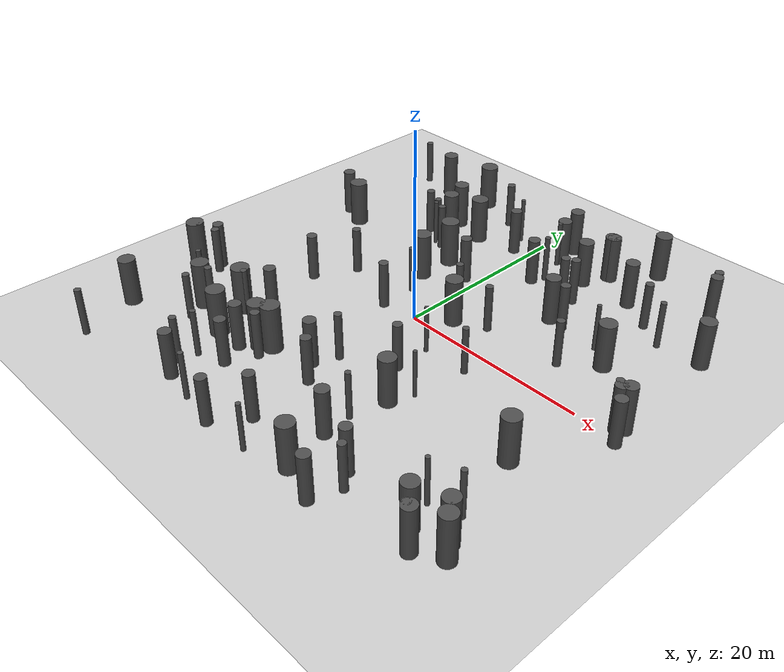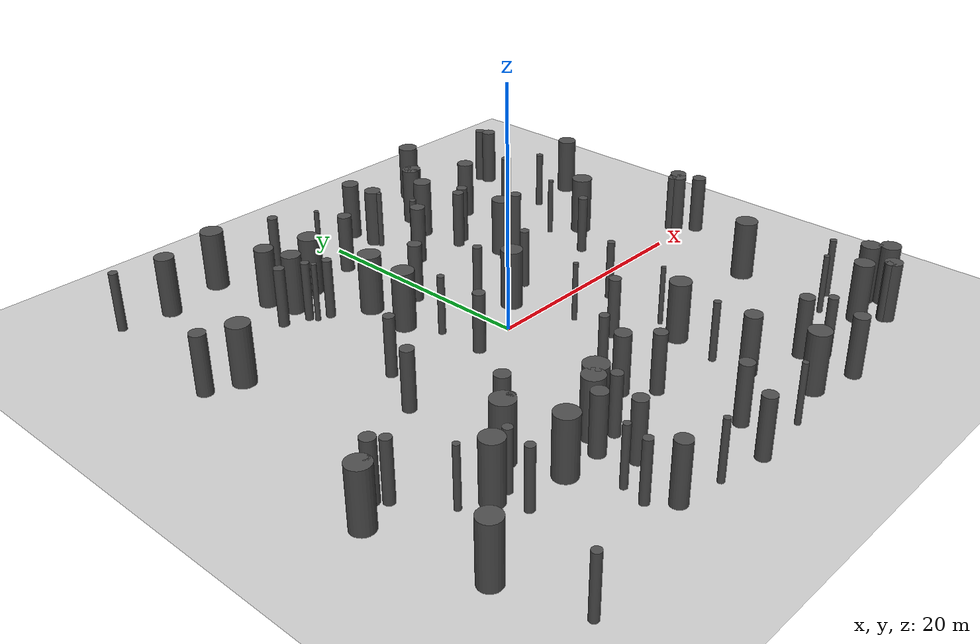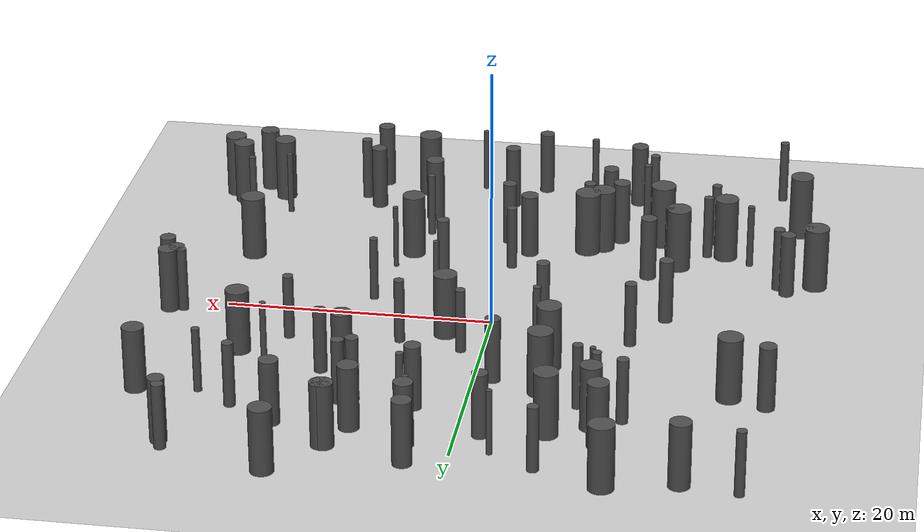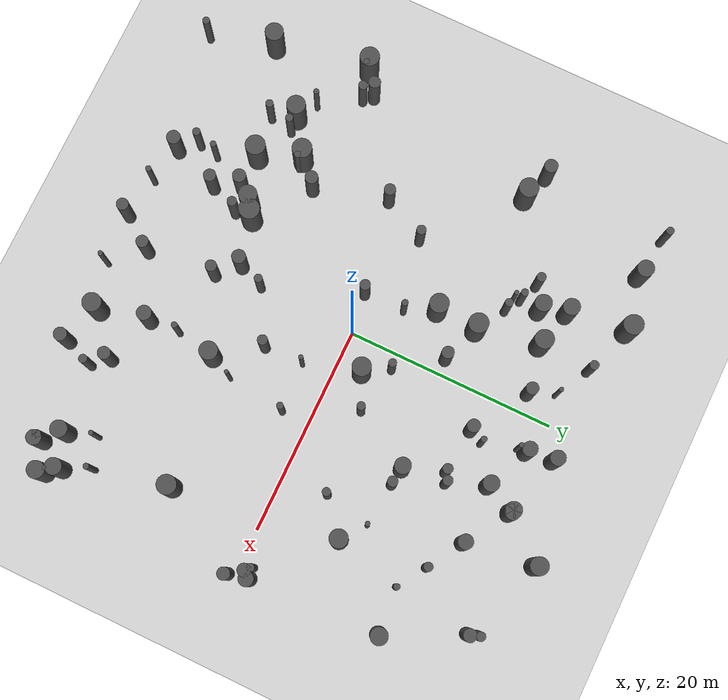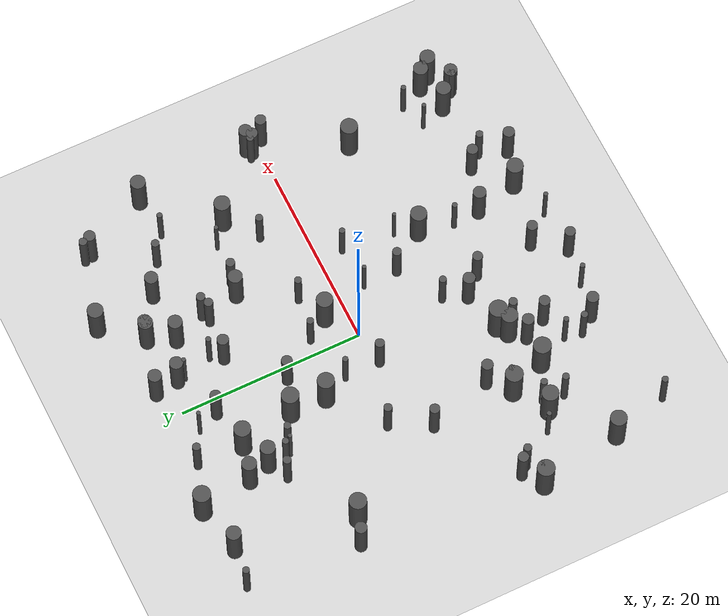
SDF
<?xml version="1.0" encoding="UTF-8"?>
<sdf version="1.9">
  <world name="default">
    <physics type="ode">
      <max_step_size>0.004</max_step_size>
      <real_time_factor>1.0</real_time_factor>
      <real_time_update_rate>250</real_time_update_rate>
    </physics>
    <gravity>0 0 -9.8</gravity>
    <magnetic_field>6e-06 2.3e-05 -4.2e-05</magnetic_field>
    <atmosphere type="adiabatic"/>
    <scene>
      <grid>false</grid>
      <ambient>0.4 0.4 0.4 1</ambient>
      <background>0.7 0.7 0.7 1</background>
      <shadows>true</shadows>
    </scene>
    <model name="ground_plane">
      <static>true</static>
      <link name="link">
        <collision name="collision">
          <geometry>
            <plane>
              <normal>0 0 1</normal>
              <size>1 1</size>
            </plane>
          </geometry>
          <surface>
            <friction>
              <ode/>
            </friction>
            <bounce/>
            <contact/>
          </surface>
        </collision>
        <visual name="visual">
          <geometry>
            <plane>
              <normal>0 0 1</normal>
              <size>500 500</size>
            </plane>
          </geometry>
          <material>
            <ambient>0.8 0.8 0.8 1</ambient>
            <diffuse>0.8 0.8 0.8 1</diffuse>
            <specular>0.8 0.8 0.8 1</specular>
          </material>
        </visual>
        <pose>0 0 0 0 -0 0</pose>
        <inertial>
          <pose>0 0 0 0 -0 0</pose>
          <mass>1</mass>
          <inertia>
            <ixx>1</ixx>
            <ixy>0</ixy>
            <ixz>0</ixz>
            <iyy>1</iyy>
            <iyz>0</iyz>
            <izz>1</izz>
          </inertia>
        </inertial>
        <enable_wind>false</enable_wind>
      </link>
      <pose>0 0 0 0 -0 0</pose>
      <self_collide>false</self_collide>
    </model>
    <light name="sunUTC" type="directional">
      <pose>0 0 500 0 -0 0</pose>
      <cast_shadows>true</cast_shadows>
      <intensity>1</intensity>
      <direction>0.001 0.625 -0.78</direction>
      <diffuse>0.904 0.904 0.904 1</diffuse>
      <specular>0.271 0.271 0.271 1</specular>
      <attenuation>
        <range>2000</range>
        <linear>0</linear>
        <constant>1</constant>
        <quadratic>0</quadratic>
      </attenuation>
      <spot>
        <inner_angle>0</inner_angle>
        <outer_angle>0</outer_angle>
        <falloff>0</falloff>
      </spot>
    </light>
    <spherical_coordinates>
      <surface_model>EARTH_WGS84</surface_model>
      <world_frame_orientation>ENU</world_frame_orientation>
      <latitude_deg>47.397971057728974</latitude_deg>
      <longitude_deg> 8.546163739800146</longitude_deg>
      <elevation>0</elevation>
    </spherical_coordinates>

    <model name='cylinder_0'>
      <static>true</static>
      <pose>19.62 -19.38 2.50 0 0 0</pose>
      <link name='link'>
        <collision name='collision'>
          <geometry>
            <cylinder>
              <radius>0.80</radius>
              <length>5.0</length>
            </cylinder>
          </geometry>
          <surface>
            <friction>
              <ode/>
            </friction>
          </surface>
        </collision>
        <visual name='visual'>
          <geometry>
            <cylinder>
              <radius>0.80</radius>
              <length>5.0</length>
            </cylinder>
          </geometry>
          <material>
            <ambient>0.3 0.3 0.3 1</ambient>
            <diffuse>0.3 0.3 0.3 1</diffuse>
            <specular>0.1 0.1 0.1 1</specular>
          </material>
        </visual>
      </link>
    </model>

    <model name='cylinder_1'>
      <static>true</static>
      <pose>-12.82 -11.24 2.50 0 0 0</pose>
      <link name='link'>
        <collision name='collision'>
          <geometry>
            <cylinder>
              <radius>0.94</radius>
              <length>5.0</length>
            </cylinder>
          </geometry>
          <surface>
            <friction>
              <ode/>
            </friction>
          </surface>
        </collision>
        <visual name='visual'>
          <geometry>
            <cylinder>
              <radius>0.94</radius>
              <length>5.0</length>
            </cylinder>
          </geometry>
          <material>
            <ambient>0.3 0.3 0.3 1</ambient>
            <diffuse>0.3 0.3 0.3 1</diffuse>
            <specular>0.1 0.1 0.1 1</specular>
          </material>
        </visual>
      </link>
    </model>

    <model name='cylinder_2'>
      <static>true</static>
      <pose>4.63 -2.87 2.50 0 0 0</pose>
      <link name='link'>
        <collision name='collision'>
          <geometry>
            <cylinder>
              <radius>0.22</radius>
              <length>5.0</length>
            </cylinder>
          </geometry>
          <surface>
            <friction>
              <ode/>
            </friction>
          </surface>
        </collision>
        <visual name='visual'>
          <geometry>
            <cylinder>
              <radius>0.22</radius>
              <length>5.0</length>
            </cylinder>
          </geometry>
          <material>
            <ambient>0.3 0.3 0.3 1</ambient>
            <diffuse>0.3 0.3 0.3 1</diffuse>
            <specular>0.1 0.1 0.1 1</specular>
          </material>
        </visual>
      </link>
    </model>

    <model name='cylinder_3'>
      <static>true</static>
      <pose>-21.10 10.03 2.50 0 0 0</pose>
      <link name='link'>
        <collision name='collision'>
          <geometry>
            <cylinder>
              <radius>0.64</radius>
              <length>5.0</length>
            </cylinder>
          </geometry>
          <surface>
            <friction>
              <ode/>
            </friction>
          </surface>
        </collision>
        <visual name='visual'>
          <geometry>
            <cylinder>
              <radius>0.64</radius>
              <length>5.0</length>
            </cylinder>
          </geometry>
          <material>
            <ambient>0.3 0.3 0.3 1</ambient>
            <diffuse>0.3 0.3 0.3 1</diffuse>
            <specular>0.1 0.1 0.1 1</specular>
          </material>
        </visual>
      </link>
    </model>

    <model name='cylinder_4'>
      <static>true</static>
      <pose>-3.78 -0.53 2.50 0 0 0</pose>
      <link name='link'>
        <collision name='collision'>
          <geometry>
            <cylinder>
              <radius>0.50</radius>
              <length>5.0</length>
            </cylinder>
          </geometry>
          <surface>
            <friction>
              <ode/>
            </friction>
          </surface>
        </collision>
        <visual name='visual'>
          <geometry>
            <cylinder>
              <radius>0.50</radius>
              <length>5.0</length>
            </cylinder>
          </geometry>
          <material>
            <ambient>0.3 0.3 0.3 1</ambient>
            <diffuse>0.3 0.3 0.3 1</diffuse>
            <specular>0.1 0.1 0.1 1</specular>
          </material>
        </visual>
      </link>
    </model>

    <model name='cylinder_5'>
      <static>true</static>
      <pose>-23.44 -9.43 2.50 0 0 0</pose>
      <link name='link'>
        <collision name='collision'>
          <geometry>
            <cylinder>
              <radius>0.93</radius>
              <length>5.0</length>
            </cylinder>
          </geometry>
          <surface>
            <friction>
              <ode/>
            </friction>
          </surface>
        </collision>
        <visual name='visual'>
          <geometry>
            <cylinder>
              <radius>0.93</radius>
              <length>5.0</length>
            </cylinder>
          </geometry>
          <material>
            <ambient>0.3 0.3 0.3 1</ambient>
            <diffuse>0.3 0.3 0.3 1</diffuse>
            <specular>0.1 0.1 0.1 1</specular>
          </material>
        </visual>
      </link>
    </model>

    <model name='cylinder_6'>
      <static>true</static>
      <pose>-1.21 -11.95 2.50 0 0 0</pose>
      <link name='link'>
        <collision name='collision'>
          <geometry>
            <cylinder>
              <radius>0.66</radius>
              <length>5.0</length>
            </cylinder>
          </geometry>
          <surface>
            <friction>
              <ode/>
            </friction>
          </surface>
        </collision>
        <visual name='visual'>
          <geometry>
            <cylinder>
              <radius>0.66</radius>
              <length>5.0</length>
            </cylinder>
          </geometry>
          <material>
            <ambient>0.3 0.3 0.3 1</ambient>
            <diffuse>0.3 0.3 0.3 1</diffuse>
            <specular>0.1 0.1 0.1 1</specular>
          </material>
        </visual>
      </link>
    </model>

    <model name='cylinder_7'>
      <static>true</static>
      <pose>-9.01 12.07 2.50 0 0 0</pose>
      <link name='link'>
        <collision name='collision'>
          <geometry>
            <cylinder>
              <radius>0.22</radius>
              <length>5.0</length>
            </cylinder>
          </geometry>
          <surface>
            <friction>
              <ode/>
            </friction>
          </surface>
        </collision>
        <visual name='visual'>
          <geometry>
            <cylinder>
              <radius>0.22</radius>
              <length>5.0</length>
            </cylinder>
          </geometry>
          <material>
            <ambient>0.3 0.3 0.3 1</ambient>
            <diffuse>0.3 0.3 0.3 1</diffuse>
            <specular>0.1 0.1 0.1 1</specular>
          </material>
        </visual>
      </link>
    </model>

    <model name='cylinder_8'>
      <static>true</static>
      <pose>-10.56 1.88 2.50 0 0 0</pose>
      <link name='link'>
        <collision name='collision'>
          <geometry>
            <cylinder>
              <radius>0.45</radius>
              <length>5.0</length>
            </cylinder>
          </geometry>
          <surface>
            <friction>
              <ode/>
            </friction>
          </surface>
        </collision>
        <visual name='visual'>
          <geometry>
            <cylinder>
              <radius>0.45</radius>
              <length>5.0</length>
            </cylinder>
          </geometry>
          <material>
            <ambient>0.3 0.3 0.3 1</ambient>
            <diffuse>0.3 0.3 0.3 1</diffuse>
            <specular>0.1 0.1 0.1 1</specular>
          </material>
        </visual>
      </link>
    </model>

    <model name='cylinder_9'>
      <static>true</static>
      <pose>-6.23 16.06 2.50 0 0 0</pose>
      <link name='link'>
        <collision name='collision'>
          <geometry>
            <cylinder>
              <radius>0.90</radius>
              <length>5.0</length>
            </cylinder>
          </geometry>
          <surface>
            <friction>
              <ode/>
            </friction>
          </surface>
        </collision>
        <visual name='visual'>
          <geometry>
            <cylinder>
              <radius>0.90</radius>
              <length>5.0</length>
            </cylinder>
          </geometry>
          <material>
            <ambient>0.3 0.3 0.3 1</ambient>
            <diffuse>0.3 0.3 0.3 1</diffuse>
            <specular>0.1 0.1 0.1 1</specular>
          </material>
        </visual>
      </link>
    </model>

    <model name='cylinder_10'>
      <static>true</static>
      <pose>-6.00 21.02 2.50 0 0 0</pose>
      <link name='link'>
        <collision name='collision'>
          <geometry>
            <cylinder>
              <radius>0.43</radius>
              <length>5.0</length>
            </cylinder>
          </geometry>
          <surface>
            <friction>
              <ode/>
            </friction>
          </surface>
        </collision>
        <visual name='visual'>
          <geometry>
            <cylinder>
              <radius>0.43</radius>
              <length>5.0</length>
            </cylinder>
          </geometry>
          <material>
            <ambient>0.3 0.3 0.3 1</ambient>
            <diffuse>0.3 0.3 0.3 1</diffuse>
            <specular>0.1 0.1 0.1 1</specular>
          </material>
        </visual>
      </link>
    </model>

    <model name='cylinder_11'>
      <static>true</static>
      <pose>-10.87 22.72 2.50 0 0 0</pose>
      <link name='link'>
        <collision name='collision'>
          <geometry>
            <cylinder>
              <radius>0.94</radius>
              <length>5.0</length>
            </cylinder>
          </geometry>
          <surface>
            <friction>
              <ode/>
            </friction>
          </surface>
        </collision>
        <visual name='visual'>
          <geometry>
            <cylinder>
              <radius>0.94</radius>
              <length>5.0</length>
            </cylinder>
          </geometry>
          <material>
            <ambient>0.3 0.3 0.3 1</ambient>
            <diffuse>0.3 0.3 0.3 1</diffuse>
            <specular>0.1 0.1 0.1 1</specular>
          </material>
        </visual>
      </link>
    </model>

    <model name='cylinder_12'>
      <static>true</static>
      <pose>-21.37 -7.94 2.50 0 0 0</pose>
      <link name='link'>
        <collision name='collision'>
          <geometry>
            <cylinder>
              <radius>0.57</radius>
              <length>5.0</length>
            </cylinder>
          </geometry>
          <surface>
            <friction>
              <ode/>
            </friction>
          </surface>
        </collision>
        <visual name='visual'>
          <geometry>
            <cylinder>
              <radius>0.57</radius>
              <length>5.0</length>
            </cylinder>
          </geometry>
          <material>
            <ambient>0.3 0.3 0.3 1</ambient>
            <diffuse>0.3 0.3 0.3 1</diffuse>
            <specular>0.1 0.1 0.1 1</specular>
          </material>
        </visual>
      </link>
    </model>

    <model name='cylinder_13'>
      <static>true</static>
      <pose>-22.87 -9.44 2.50 0 0 0</pose>
      <link name='link'>
        <collision name='collision'>
          <geometry>
            <cylinder>
              <radius>0.32</radius>
              <length>5.0</length>
            </cylinder>
          </geometry>
          <surface>
            <friction>
              <ode/>
            </friction>
          </surface>
        </collision>
        <visual name='visual'>
          <geometry>
            <cylinder>
              <radius>0.32</radius>
              <length>5.0</length>
            </cylinder>
          </geometry>
          <material>
            <ambient>0.3 0.3 0.3 1</ambient>
            <diffuse>0.3 0.3 0.3 1</diffuse>
            <specular>0.1 0.1 0.1 1</specular>
          </material>
        </visual>
      </link>
    </model>

    <model name='cylinder_14'>
      <static>true</static>
      <pose>23.16 1.25 2.50 0 0 0</pose>
      <link name='link'>
        <collision name='collision'>
          <geometry>
            <cylinder>
              <radius>0.38</radius>
              <length>5.0</length>
            </cylinder>
          </geometry>
          <surface>
            <friction>
              <ode/>
            </friction>
          </surface>
        </collision>
        <visual name='visual'>
          <geometry>
            <cylinder>
              <radius>0.38</radius>
              <length>5.0</length>
            </cylinder>
          </geometry>
          <material>
            <ambient>0.3 0.3 0.3 1</ambient>
            <diffuse>0.3 0.3 0.3 1</diffuse>
            <specular>0.1 0.1 0.1 1</specular>
          </material>
        </visual>
      </link>
    </model>

    <model name='cylinder_15'>
      <static>true</static>
      <pose>16.44 15.20 2.50 0 0 0</pose>
      <link name='link'>
        <collision name='collision'>
          <geometry>
            <cylinder>
              <radius>0.43</radius>
              <length>5.0</length>
            </cylinder>
          </geometry>
          <surface>
            <friction>
              <ode/>
            </friction>
          </surface>
        </collision>
        <visual name='visual'>
          <geometry>
            <cylinder>
              <radius>0.43</radius>
              <length>5.0</length>
            </cylinder>
          </geometry>
          <material>
            <ambient>0.3 0.3 0.3 1</ambient>
            <diffuse>0.3 0.3 0.3 1</diffuse>
            <specular>0.1 0.1 0.1 1</specular>
          </material>
        </visual>
      </link>
    </model>

    <model name='cylinder_16'>
      <static>true</static>
      <pose>9.44 9.45 2.50 0 0 0</pose>
      <link name='link'>
        <collision name='collision'>
          <geometry>
            <cylinder>
              <radius>0.77</radius>
              <length>5.0</length>
            </cylinder>
          </geometry>
          <surface>
            <friction>
              <ode/>
            </friction>
          </surface>
        </collision>
        <visual name='visual'>
          <geometry>
            <cylinder>
              <radius>0.77</radius>
              <length>5.0</length>
            </cylinder>
          </geometry>
          <material>
            <ambient>0.3 0.3 0.3 1</ambient>
            <diffuse>0.3 0.3 0.3 1</diffuse>
            <specular>0.1 0.1 0.1 1</specular>
          </material>
        </visual>
      </link>
    </model>

    <model name='cylinder_17'>
      <static>true</static>
      <pose>-2.74 19.27 2.50 0 0 0</pose>
      <link name='link'>
        <collision name='collision'>
          <geometry>
            <cylinder>
              <radius>0.22</radius>
              <length>5.0</length>
            </cylinder>
          </geometry>
          <surface>
            <friction>
              <ode/>
            </friction>
          </surface>
        </collision>
        <visual name='visual'>
          <geometry>
            <cylinder>
              <radius>0.22</radius>
              <length>5.0</length>
            </cylinder>
          </geometry>
          <material>
            <ambient>0.3 0.3 0.3 1</ambient>
            <diffuse>0.3 0.3 0.3 1</diffuse>
            <specular>0.1 0.1 0.1 1</specular>
          </material>
        </visual>
      </link>
    </model>

    <model name='cylinder_18'>
      <static>true</static>
      <pose>11.87 -18.88 2.50 0 0 0</pose>
      <link name='link'>
        <collision name='collision'>
          <geometry>
            <cylinder>
              <radius>0.60</radius>
              <length>5.0</length>
            </cylinder>
          </geometry>
          <surface>
            <friction>
              <ode/>
            </friction>
          </surface>
        </collision>
        <visual name='visual'>
          <geometry>
            <cylinder>
              <radius>0.60</radius>
              <length>5.0</length>
            </cylinder>
          </geometry>
          <material>
            <ambient>0.3 0.3 0.3 1</ambient>
            <diffuse>0.3 0.3 0.3 1</diffuse>
            <specular>0.1 0.1 0.1 1</specular>
          </material>
        </visual>
      </link>
    </model>

    <model name='cylinder_19'>
      <static>true</static>
      <pose>-7.90 11.83 2.50 0 0 0</pose>
      <link name='link'>
        <collision name='collision'>
          <geometry>
            <cylinder>
              <radius>0.39</radius>
              <length>5.0</length>
            </cylinder>
          </geometry>
          <surface>
            <friction>
              <ode/>
            </friction>
          </surface>
        </collision>
        <visual name='visual'>
          <geometry>
            <cylinder>
              <radius>0.39</radius>
              <length>5.0</length>
            </cylinder>
          </geometry>
          <material>
            <ambient>0.3 0.3 0.3 1</ambient>
            <diffuse>0.3 0.3 0.3 1</diffuse>
            <specular>0.1 0.1 0.1 1</specular>
          </material>
        </visual>
      </link>
    </model>

    <model name='cylinder_20'>
      <static>true</static>
      <pose>19.85 21.79 2.50 0 0 0</pose>
      <link name='link'>
        <collision name='collision'>
          <geometry>
            <cylinder>
              <radius>0.44</radius>
              <length>5.0</length>
            </cylinder>
          </geometry>
          <surface>
            <friction>
              <ode/>
            </friction>
          </surface>
        </collision>
        <visual name='visual'>
          <geometry>
            <cylinder>
              <radius>0.44</radius>
              <length>5.0</length>
            </cylinder>
          </geometry>
          <material>
            <ambient>0.3 0.3 0.3 1</ambient>
            <diffuse>0.3 0.3 0.3 1</diffuse>
            <specular>0.1 0.1 0.1 1</specular>
          </material>
        </visual>
      </link>
    </model>

    <model name='cylinder_21'>
      <static>true</static>
      <pose>-1.72 16.91 2.50 0 0 0</pose>
      <link name='link'>
        <collision name='collision'>
          <geometry>
            <cylinder>
              <radius>0.59</radius>
              <length>5.0</length>
            </cylinder>
          </geometry>
          <surface>
            <friction>
              <ode/>
            </friction>
          </surface>
        </collision>
        <visual name='visual'>
          <geometry>
            <cylinder>
              <radius>0.59</radius>
              <length>5.0</length>
            </cylinder>
          </geometry>
          <material>
            <ambient>0.3 0.3 0.3 1</ambient>
            <diffuse>0.3 0.3 0.3 1</diffuse>
            <specular>0.1 0.1 0.1 1</specular>
          </material>
        </visual>
      </link>
    </model>

    <model name='cylinder_22'>
      <static>true</static>
      <pose>4.25 14.92 2.50 0 0 0</pose>
      <link name='link'>
        <collision name='collision'>
          <geometry>
            <cylinder>
              <radius>0.29</radius>
              <length>5.0</length>
            </cylinder>
          </geometry>
          <surface>
            <friction>
              <ode/>
            </friction>
          </surface>
        </collision>
        <visual name='visual'>
          <geometry>
            <cylinder>
              <radius>0.29</radius>
              <length>5.0</length>
            </cylinder>
          </geometry>
          <material>
            <ambient>0.3 0.3 0.3 1</ambient>
            <diffuse>0.3 0.3 0.3 1</diffuse>
            <specular>0.1 0.1 0.1 1</specular>
          </material>
        </visual>
      </link>
    </model>

    <model name='cylinder_23'>
      <static>true</static>
      <pose>1.57 4.73 2.50 0 0 0</pose>
      <link name='link'>
        <collision name='collision'>
          <geometry>
            <cylinder>
              <radius>0.38</radius>
              <length>5.0</length>
            </cylinder>
          </geometry>
          <surface>
            <friction>
              <ode/>
            </friction>
          </surface>
        </collision>
        <visual name='visual'>
          <geometry>
            <cylinder>
              <radius>0.38</radius>
              <length>5.0</length>
            </cylinder>
          </geometry>
          <material>
            <ambient>0.3 0.3 0.3 1</ambient>
            <diffuse>0.3 0.3 0.3 1</diffuse>
            <specular>0.1 0.1 0.1 1</specular>
          </material>
        </visual>
      </link>
    </model>

    <model name='cylinder_24'>
      <static>true</static>
      <pose>-8.00 -15.27 2.50 0 0 0</pose>
      <link name='link'>
        <collision name='collision'>
          <geometry>
            <cylinder>
              <radius>0.64</radius>
              <length>5.0</length>
            </cylinder>
          </geometry>
          <surface>
            <friction>
              <ode/>
            </friction>
          </surface>
        </collision>
        <visual name='visual'>
          <geometry>
            <cylinder>
              <radius>0.64</radius>
              <length>5.0</length>
            </cylinder>
          </geometry>
          <material>
            <ambient>0.3 0.3 0.3 1</ambient>
            <diffuse>0.3 0.3 0.3 1</diffuse>
            <specular>0.1 0.1 0.1 1</specular>
          </material>
        </visual>
      </link>
    </model>

    <model name='cylinder_25'>
      <static>true</static>
      <pose>-6.87 -17.71 2.50 0 0 0</pose>
      <link name='link'>
        <collision name='collision'>
          <geometry>
            <cylinder>
              <radius>0.59</radius>
              <length>5.0</length>
            </cylinder>
          </geometry>
          <surface>
            <friction>
              <ode/>
            </friction>
          </surface>
        </collision>
        <visual name='visual'>
          <geometry>
            <cylinder>
              <radius>0.59</radius>
              <length>5.0</length>
            </cylinder>
          </geometry>
          <material>
            <ambient>0.3 0.3 0.3 1</ambient>
            <diffuse>0.3 0.3 0.3 1</diffuse>
            <specular>0.1 0.1 0.1 1</specular>
          </material>
        </visual>
      </link>
    </model>

    <model name='cylinder_26'>
      <static>true</static>
      <pose>-5.02 10.14 2.50 0 0 0</pose>
      <link name='link'>
        <collision name='collision'>
          <geometry>
            <cylinder>
              <radius>0.94</radius>
              <length>5.0</length>
            </cylinder>
          </geometry>
          <surface>
            <friction>
              <ode/>
            </friction>
          </surface>
        </collision>
        <visual name='visual'>
          <geometry>
            <cylinder>
              <radius>0.94</radius>
              <length>5.0</length>
            </cylinder>
          </geometry>
          <material>
            <ambient>0.3 0.3 0.3 1</ambient>
            <diffuse>0.3 0.3 0.3 1</diffuse>
            <specular>0.1 0.1 0.1 1</specular>
          </material>
        </visual>
      </link>
    </model>

    <model name='cylinder_27'>
      <static>true</static>
      <pose>12.03 -23.19 2.50 0 0 0</pose>
      <link name='link'>
        <collision name='collision'>
          <geometry>
            <cylinder>
              <radius>0.63</radius>
              <length>5.0</length>
            </cylinder>
          </geometry>
          <surface>
            <friction>
              <ode/>
            </friction>
          </surface>
        </collision>
        <visual name='visual'>
          <geometry>
            <cylinder>
              <radius>0.63</radius>
              <length>5.0</length>
            </cylinder>
          </geometry>
          <material>
            <ambient>0.3 0.3 0.3 1</ambient>
            <diffuse>0.3 0.3 0.3 1</diffuse>
            <specular>0.1 0.1 0.1 1</specular>
          </material>
        </visual>
      </link>
    </model>

    <model name='cylinder_28'>
      <static>true</static>
      <pose>-18.26 -12.42 2.50 0 0 0</pose>
      <link name='link'>
        <collision name='collision'>
          <geometry>
            <cylinder>
              <radius>0.26</radius>
              <length>5.0</length>
            </cylinder>
          </geometry>
          <surface>
            <friction>
              <ode/>
            </friction>
          </surface>
        </collision>
        <visual name='visual'>
          <geometry>
            <cylinder>
              <radius>0.26</radius>
              <length>5.0</length>
            </cylinder>
          </geometry>
          <material>
            <ambient>0.3 0.3 0.3 1</ambient>
            <diffuse>0.3 0.3 0.3 1</diffuse>
            <specular>0.1 0.1 0.1 1</specular>
          </material>
        </visual>
      </link>
    </model>

    <model name='cylinder_29'>
      <static>true</static>
      <pose>3.27 18.96 2.50 0 0 0</pose>
      <link name='link'>
        <collision name='collision'>
          <geometry>
            <cylinder>
              <radius>0.71</radius>
              <length>5.0</length>
            </cylinder>
          </geometry>
          <surface>
            <friction>
              <ode/>
            </friction>
          </surface>
        </collision>
        <visual name='visual'>
          <geometry>
            <cylinder>
              <radius>0.71</radius>
              <length>5.0</length>
            </cylinder>
          </geometry>
          <material>
            <ambient>0.3 0.3 0.3 1</ambient>
            <diffuse>0.3 0.3 0.3 1</diffuse>
            <specular>0.1 0.1 0.1 1</specular>
          </material>
        </visual>
      </link>
    </model>

    <model name='cylinder_30'>
      <static>true</static>
      <pose>-5.02 -23.02 2.50 0 0 0</pose>
      <link name='link'>
        <collision name='collision'>
          <geometry>
            <cylinder>
              <radius>0.27</radius>
              <length>5.0</length>
            </cylinder>
          </geometry>
          <surface>
            <friction>
              <ode/>
            </friction>
          </surface>
        </collision>
        <visual name='visual'>
          <geometry>
            <cylinder>
              <radius>0.27</radius>
              <length>5.0</length>
            </cylinder>
          </geometry>
          <material>
            <ambient>0.3 0.3 0.3 1</ambient>
            <diffuse>0.3 0.3 0.3 1</diffuse>
            <specular>0.1 0.1 0.1 1</specular>
          </material>
        </visual>
      </link>
    </model>

    <model name='cylinder_31'>
      <static>true</static>
      <pose>-16.06 21.65 2.50 0 0 0</pose>
      <link name='link'>
        <collision name='collision'>
          <geometry>
            <cylinder>
              <radius>0.79</radius>
              <length>5.0</length>
            </cylinder>
          </geometry>
          <surface>
            <friction>
              <ode/>
            </friction>
          </surface>
        </collision>
        <visual name='visual'>
          <geometry>
            <cylinder>
              <radius>0.79</radius>
              <length>5.0</length>
            </cylinder>
          </geometry>
          <material>
            <ambient>0.3 0.3 0.3 1</ambient>
            <diffuse>0.3 0.3 0.3 1</diffuse>
            <specular>0.1 0.1 0.1 1</specular>
          </material>
        </visual>
      </link>
    </model>

    <model name='cylinder_32'>
      <static>true</static>
      <pose>-11.24 -15.23 2.50 0 0 0</pose>
      <link name='link'>
        <collision name='collision'>
          <geometry>
            <cylinder>
              <radius>0.95</radius>
              <length>5.0</length>
            </cylinder>
          </geometry>
          <surface>
            <friction>
              <ode/>
            </friction>
          </surface>
        </collision>
        <visual name='visual'>
          <geometry>
            <cylinder>
              <radius>0.95</radius>
              <length>5.0</length>
            </cylinder>
          </geometry>
          <material>
            <ambient>0.3 0.3 0.3 1</ambient>
            <diffuse>0.3 0.3 0.3 1</diffuse>
            <specular>0.1 0.1 0.1 1</specular>
          </material>
        </visual>
      </link>
    </model>

    <model name='cylinder_33'>
      <static>true</static>
      <pose>20.17 20.92 2.50 0 0 0</pose>
      <link name='link'>
        <collision name='collision'>
          <geometry>
            <cylinder>
              <radius>0.62</radius>
              <length>5.0</length>
            </cylinder>
          </geometry>
          <surface>
            <friction>
              <ode/>
            </friction>
          </surface>
        </collision>
        <visual name='visual'>
          <geometry>
            <cylinder>
              <radius>0.62</radius>
              <length>5.0</length>
            </cylinder>
          </geometry>
          <material>
            <ambient>0.3 0.3 0.3 1</ambient>
            <diffuse>0.3 0.3 0.3 1</diffuse>
            <specular>0.1 0.1 0.1 1</specular>
          </material>
        </visual>
      </link>
    </model>

    <model name='cylinder_34'>
      <static>true</static>
      <pose>21.51 -15.66 2.50 0 0 0</pose>
      <link name='link'>
        <collision name='collision'>
          <geometry>
            <cylinder>
              <radius>0.28</radius>
              <length>5.0</length>
            </cylinder>
          </geometry>
          <surface>
            <friction>
              <ode/>
            </friction>
          </surface>
        </collision>
        <visual name='visual'>
          <geometry>
            <cylinder>
              <radius>0.28</radius>
              <length>5.0</length>
            </cylinder>
          </geometry>
          <material>
            <ambient>0.3 0.3 0.3 1</ambient>
            <diffuse>0.3 0.3 0.3 1</diffuse>
            <specular>0.1 0.1 0.1 1</specular>
          </material>
        </visual>
      </link>
    </model>

    <model name='cylinder_35'>
      <static>true</static>
      <pose>-0.17 -9.47 2.50 0 0 0</pose>
      <link name='link'>
        <collision name='collision'>
          <geometry>
            <cylinder>
              <radius>0.39</radius>
              <length>5.0</length>
            </cylinder>
          </geometry>
          <surface>
            <friction>
              <ode/>
            </friction>
          </surface>
        </collision>
        <visual name='visual'>
          <geometry>
            <cylinder>
              <radius>0.39</radius>
              <length>5.0</length>
            </cylinder>
          </geometry>
          <material>
            <ambient>0.3 0.3 0.3 1</ambient>
            <diffuse>0.3 0.3 0.3 1</diffuse>
            <specular>0.1 0.1 0.1 1</specular>
          </material>
        </visual>
      </link>
    </model>

    <model name='cylinder_36'>
      <static>true</static>
      <pose>-15.35 -15.80 2.50 0 0 0</pose>
      <link name='link'>
        <collision name='collision'>
          <geometry>
            <cylinder>
              <radius>0.37</radius>
              <length>5.0</length>
            </cylinder>
          </geometry>
          <surface>
            <friction>
              <ode/>
            </friction>
          </surface>
        </collision>
        <visual name='visual'>
          <geometry>
            <cylinder>
              <radius>0.37</radius>
              <length>5.0</length>
            </cylinder>
          </geometry>
          <material>
            <ambient>0.3 0.3 0.3 1</ambient>
            <diffuse>0.3 0.3 0.3 1</diffuse>
            <specular>0.1 0.1 0.1 1</specular>
          </material>
        </visual>
      </link>
    </model>

    <model name='cylinder_37'>
      <static>true</static>
      <pose>-5.14 6.20 2.50 0 0 0</pose>
      <link name='link'>
        <collision name='collision'>
          <geometry>
            <cylinder>
              <radius>0.91</radius>
              <length>5.0</length>
            </cylinder>
          </geometry>
          <surface>
            <friction>
              <ode/>
            </friction>
          </surface>
        </collision>
        <visual name='visual'>
          <geometry>
            <cylinder>
              <radius>0.91</radius>
              <length>5.0</length>
            </cylinder>
          </geometry>
          <material>
            <ambient>0.3 0.3 0.3 1</ambient>
            <diffuse>0.3 0.3 0.3 1</diffuse>
            <specular>0.1 0.1 0.1 1</specular>
          </material>
        </visual>
      </link>
    </model>

    <model name='cylinder_38'>
      <static>true</static>
      <pose>4.71 -6.65 2.50 0 0 0</pose>
      <link name='link'>
        <collision name='collision'>
          <geometry>
            <cylinder>
              <radius>0.48</radius>
              <length>5.0</length>
            </cylinder>
          </geometry>
          <surface>
            <friction>
              <ode/>
            </friction>
          </surface>
        </collision>
        <visual name='visual'>
          <geometry>
            <cylinder>
              <radius>0.48</radius>
              <length>5.0</length>
            </cylinder>
          </geometry>
          <material>
            <ambient>0.3 0.3 0.3 1</ambient>
            <diffuse>0.3 0.3 0.3 1</diffuse>
            <specular>0.1 0.1 0.1 1</specular>
          </material>
        </visual>
      </link>
    </model>

    <model name='cylinder_39'>
      <static>true</static>
      <pose>-9.34 12.72 2.50 0 0 0</pose>
      <link name='link'>
        <collision name='collision'>
          <geometry>
            <cylinder>
              <radius>0.35</radius>
              <length>5.0</length>
            </cylinder>
          </geometry>
          <surface>
            <friction>
              <ode/>
            </friction>
          </surface>
        </collision>
        <visual name='visual'>
          <geometry>
            <cylinder>
              <radius>0.35</radius>
              <length>5.0</length>
            </cylinder>
          </geometry>
          <material>
            <ambient>0.3 0.3 0.3 1</ambient>
            <diffuse>0.3 0.3 0.3 1</diffuse>
            <specular>0.1 0.1 0.1 1</specular>
          </material>
        </visual>
      </link>
    </model>

    <model name='cylinder_40'>
      <static>true</static>
      <pose>19.16 13.46 2.50 0 0 0</pose>
      <link name='link'>
        <collision name='collision'>
          <geometry>
            <cylinder>
              <radius>0.30</radius>
              <length>5.0</length>
            </cylinder>
          </geometry>
          <surface>
            <friction>
              <ode/>
            </friction>
          </surface>
        </collision>
        <visual name='visual'>
          <geometry>
            <cylinder>
              <radius>0.30</radius>
              <length>5.0</length>
            </cylinder>
          </geometry>
          <material>
            <ambient>0.3 0.3 0.3 1</ambient>
            <diffuse>0.3 0.3 0.3 1</diffuse>
            <specular>0.1 0.1 0.1 1</specular>
          </material>
        </visual>
      </link>
    </model>

    <model name='cylinder_41'>
      <static>true</static>
      <pose>24.63 -0.62 2.50 0 0 0</pose>
      <link name='link'>
        <collision name='collision'>
          <geometry>
            <cylinder>
              <radius>0.60</radius>
              <length>5.0</length>
            </cylinder>
          </geometry>
          <surface>
            <friction>
              <ode/>
            </friction>
          </surface>
        </collision>
        <visual name='visual'>
          <geometry>
            <cylinder>
              <radius>0.60</radius>
              <length>5.0</length>
            </cylinder>
          </geometry>
          <material>
            <ambient>0.3 0.3 0.3 1</ambient>
            <diffuse>0.3 0.3 0.3 1</diffuse>
            <specular>0.1 0.1 0.1 1</specular>
          </material>
        </visual>
      </link>
    </model>

    <model name='cylinder_42'>
      <static>true</static>
      <pose>3.55 13.61 2.50 0 0 0</pose>
      <link name='link'>
        <collision name='collision'>
          <geometry>
            <cylinder>
              <radius>0.62</radius>
              <length>5.0</length>
            </cylinder>
          </geometry>
          <surface>
            <friction>
              <ode/>
            </friction>
          </surface>
        </collision>
        <visual name='visual'>
          <geometry>
            <cylinder>
              <radius>0.62</radius>
              <length>5.0</length>
            </cylinder>
          </geometry>
          <material>
            <ambient>0.3 0.3 0.3 1</ambient>
            <diffuse>0.3 0.3 0.3 1</diffuse>
            <specular>0.1 0.1 0.1 1</specular>
          </material>
        </visual>
      </link>
    </model>

    <model name='cylinder_43'>
      <static>true</static>
      <pose>0.63 -13.84 2.50 0 0 0</pose>
      <link name='link'>
        <collision name='collision'>
          <geometry>
            <cylinder>
              <radius>0.54</radius>
              <length>5.0</length>
            </cylinder>
          </geometry>
          <surface>
            <friction>
              <ode/>
            </friction>
          </surface>
        </collision>
        <visual name='visual'>
          <geometry>
            <cylinder>
              <radius>0.54</radius>
              <length>5.0</length>
            </cylinder>
          </geometry>
          <material>
            <ambient>0.3 0.3 0.3 1</ambient>
            <diffuse>0.3 0.3 0.3 1</diffuse>
            <specular>0.1 0.1 0.1 1</specular>
          </material>
        </visual>
      </link>
    </model>

    <model name='cylinder_44'>
      <static>true</static>
      <pose>6.89 -14.36 2.50 0 0 0</pose>
      <link name='link'>
        <collision name='collision'>
          <geometry>
            <cylinder>
              <radius>0.29</radius>
              <length>5.0</length>
            </cylinder>
          </geometry>
          <surface>
            <friction>
              <ode/>
            </friction>
          </surface>
        </collision>
        <visual name='visual'>
          <geometry>
            <cylinder>
              <radius>0.29</radius>
              <length>5.0</length>
            </cylinder>
          </geometry>
          <material>
            <ambient>0.3 0.3 0.3 1</ambient>
            <diffuse>0.3 0.3 0.3 1</diffuse>
            <specular>0.1 0.1 0.1 1</specular>
          </material>
        </visual>
      </link>
    </model>

    <model name='cylinder_45'>
      <static>true</static>
      <pose>-1.02 -23.64 2.50 0 0 0</pose>
      <link name='link'>
        <collision name='collision'>
          <geometry>
            <cylinder>
              <radius>0.57</radius>
              <length>5.0</length>
            </cylinder>
          </geometry>
          <surface>
            <friction>
              <ode/>
            </friction>
          </surface>
        </collision>
        <visual name='visual'>
          <geometry>
            <cylinder>
              <radius>0.57</radius>
              <length>5.0</length>
            </cylinder>
          </geometry>
          <material>
            <ambient>0.3 0.3 0.3 1</ambient>
            <diffuse>0.3 0.3 0.3 1</diffuse>
            <specular>0.1 0.1 0.1 1</specular>
          </material>
        </visual>
      </link>
    </model>

    <model name='cylinder_46'>
      <static>true</static>
      <pose>-3.85 3.39 2.50 0 0 0</pose>
      <link name='link'>
        <collision name='collision'>
          <geometry>
            <cylinder>
              <radius>0.30</radius>
              <length>5.0</length>
            </cylinder>
          </geometry>
          <surface>
            <friction>
              <ode/>
            </friction>
          </surface>
        </collision>
        <visual name='visual'>
          <geometry>
            <cylinder>
              <radius>0.30</radius>
              <length>5.0</length>
            </cylinder>
          </geometry>
          <material>
            <ambient>0.3 0.3 0.3 1</ambient>
            <diffuse>0.3 0.3 0.3 1</diffuse>
            <specular>0.1 0.1 0.1 1</specular>
          </material>
        </visual>
      </link>
    </model>

    <model name='cylinder_47'>
      <static>true</static>
      <pose>13.08 17.22 2.50 0 0 0</pose>
      <link name='link'>
        <collision name='collision'>
          <geometry>
            <cylinder>
              <radius>0.71</radius>
              <length>5.0</length>
            </cylinder>
          </geometry>
          <surface>
            <friction>
              <ode/>
            </friction>
          </surface>
        </collision>
        <visual name='visual'>
          <geometry>
            <cylinder>
              <radius>0.71</radius>
              <length>5.0</length>
            </cylinder>
          </geometry>
          <material>
            <ambient>0.3 0.3 0.3 1</ambient>
            <diffuse>0.3 0.3 0.3 1</diffuse>
            <specular>0.1 0.1 0.1 1</specular>
          </material>
        </visual>
      </link>
    </model>

    <model name='cylinder_48'>
      <static>true</static>
      <pose>-12.75 -2.30 2.50 0 0 0</pose>
      <link name='link'>
        <collision name='collision'>
          <geometry>
            <cylinder>
              <radius>0.54</radius>
              <length>5.0</length>
            </cylinder>
          </geometry>
          <surface>
            <friction>
              <ode/>
            </friction>
          </surface>
        </collision>
        <visual name='visual'>
          <geometry>
            <cylinder>
              <radius>0.54</radius>
              <length>5.0</length>
            </cylinder>
          </geometry>
          <material>
            <ambient>0.3 0.3 0.3 1</ambient>
            <diffuse>0.3 0.3 0.3 1</diffuse>
            <specular>0.1 0.1 0.1 1</specular>
          </material>
        </visual>
      </link>
    </model>

    <model name='cylinder_49'>
      <static>true</static>
      <pose>-11.27 13.48 2.50 0 0 0</pose>
      <link name='link'>
        <collision name='collision'>
          <geometry>
            <cylinder>
              <radius>0.44</radius>
              <length>5.0</length>
            </cylinder>
          </geometry>
          <surface>
            <friction>
              <ode/>
            </friction>
          </surface>
        </collision>
        <visual name='visual'>
          <geometry>
            <cylinder>
              <radius>0.44</radius>
              <length>5.0</length>
            </cylinder>
          </geometry>
          <material>
            <ambient>0.3 0.3 0.3 1</ambient>
            <diffuse>0.3 0.3 0.3 1</diffuse>
            <specular>0.1 0.1 0.1 1</specular>
          </material>
        </visual>
      </link>
    </model>

    <model name='cylinder_50'>
      <static>true</static>
      <pose>-6.76 -13.78 2.50 0 0 0</pose>
      <link name='link'>
        <collision name='collision'>
          <geometry>
            <cylinder>
              <radius>0.88</radius>
              <length>5.0</length>
            </cylinder>
          </geometry>
          <surface>
            <friction>
              <ode/>
            </friction>
          </surface>
        </collision>
        <visual name='visual'>
          <geometry>
            <cylinder>
              <radius>0.88</radius>
              <length>5.0</length>
            </cylinder>
          </geometry>
          <material>
            <ambient>0.3 0.3 0.3 1</ambient>
            <diffuse>0.3 0.3 0.3 1</diffuse>
            <specular>0.1 0.1 0.1 1</specular>
          </material>
        </visual>
      </link>
    </model>

    <model name='cylinder_51'>
      <static>true</static>
      <pose>19.90 -8.57 2.50 0 0 0</pose>
      <link name='link'>
        <collision name='collision'>
          <geometry>
            <cylinder>
              <radius>0.92</radius>
              <length>5.0</length>
            </cylinder>
          </geometry>
          <surface>
            <friction>
              <ode/>
            </friction>
          </surface>
        </collision>
        <visual name='visual'>
          <geometry>
            <cylinder>
              <radius>0.92</radius>
              <length>5.0</length>
            </cylinder>
          </geometry>
          <material>
            <ambient>0.3 0.3 0.3 1</ambient>
            <diffuse>0.3 0.3 0.3 1</diffuse>
            <specular>0.1 0.1 0.1 1</specular>
          </material>
        </visual>
      </link>
    </model>

    <model name='cylinder_52'>
      <static>true</static>
      <pose>8.94 19.87 2.50 0 0 0</pose>
      <link name='link'>
        <collision name='collision'>
          <geometry>
            <cylinder>
              <radius>0.73</radius>
              <length>5.0</length>
            </cylinder>
          </geometry>
          <surface>
            <friction>
              <ode/>
            </friction>
          </surface>
        </collision>
        <visual name='visual'>
          <geometry>
            <cylinder>
              <radius>0.73</radius>
              <length>5.0</length>
            </cylinder>
          </geometry>
          <material>
            <ambient>0.3 0.3 0.3 1</ambient>
            <diffuse>0.3 0.3 0.3 1</diffuse>
            <specular>0.1 0.1 0.1 1</specular>
          </material>
        </visual>
      </link>
    </model>

    <model name='cylinder_53'>
      <static>true</static>
      <pose>9.34 -2.64 2.50 0 0 0</pose>
      <link name='link'>
        <collision name='collision'>
          <geometry>
            <cylinder>
              <radius>0.32</radius>
              <length>5.0</length>
            </cylinder>
          </geometry>
          <surface>
            <friction>
              <ode/>
            </friction>
          </surface>
        </collision>
        <visual name='visual'>
          <geometry>
            <cylinder>
              <radius>0.32</radius>
              <length>5.0</length>
            </cylinder>
          </geometry>
          <material>
            <ambient>0.3 0.3 0.3 1</ambient>
            <diffuse>0.3 0.3 0.3 1</diffuse>
            <specular>0.1 0.1 0.1 1</specular>
          </material>
        </visual>
      </link>
    </model>

    <model name='cylinder_54'>
      <static>true</static>
      <pose>-5.61 -13.07 2.50 0 0 0</pose>
      <link name='link'>
        <collision name='collision'>
          <geometry>
            <cylinder>
              <radius>0.98</radius>
              <length>5.0</length>
            </cylinder>
          </geometry>
          <surface>
            <friction>
              <ode/>
            </friction>
          </surface>
        </collision>
        <visual name='visual'>
          <geometry>
            <cylinder>
              <radius>0.98</radius>
              <length>5.0</length>
            </cylinder>
          </geometry>
          <material>
            <ambient>0.3 0.3 0.3 1</ambient>
            <diffuse>0.3 0.3 0.3 1</diffuse>
            <specular>0.1 0.1 0.1 1</specular>
          </material>
        </visual>
      </link>
    </model>

    <model name='cylinder_55'>
      <static>true</static>
      <pose>21.24 -21.02 2.50 0 0 0</pose>
      <link name='link'>
        <collision name='collision'>
          <geometry>
            <cylinder>
              <radius>0.71</radius>
              <length>5.0</length>
            </cylinder>
          </geometry>
          <surface>
            <friction>
              <ode/>
            </friction>
          </surface>
        </collision>
        <visual name='visual'>
          <geometry>
            <cylinder>
              <radius>0.71</radius>
              <length>5.0</length>
            </cylinder>
          </geometry>
          <material>
            <ambient>0.3 0.3 0.3 1</ambient>
            <diffuse>0.3 0.3 0.3 1</diffuse>
            <specular>0.1 0.1 0.1 1</specular>
          </material>
        </visual>
      </link>
    </model>

    <model name='cylinder_56'>
      <static>true</static>
      <pose>3.28 18.13 2.50 0 0 0</pose>
      <link name='link'>
        <collision name='collision'>
          <geometry>
            <cylinder>
              <radius>0.23</radius>
              <length>5.0</length>
            </cylinder>
          </geometry>
          <surface>
            <friction>
              <ode/>
            </friction>
          </surface>
        </collision>
        <visual name='visual'>
          <geometry>
            <cylinder>
              <radius>0.23</radius>
              <length>5.0</length>
            </cylinder>
          </geometry>
          <material>
            <ambient>0.3 0.3 0.3 1</ambient>
            <diffuse>0.3 0.3 0.3 1</diffuse>
            <specular>0.1 0.1 0.1 1</specular>
          </material>
        </visual>
      </link>
    </model>

    <model name='cylinder_57'>
      <static>true</static>
      <pose>7.65 -10.58 2.50 0 0 0</pose>
      <link name='link'>
        <collision name='collision'>
          <geometry>
            <cylinder>
              <radius>0.87</radius>
              <length>5.0</length>
            </cylinder>
          </geometry>
          <surface>
            <friction>
              <ode/>
            </friction>
          </surface>
        </collision>
        <visual name='visual'>
          <geometry>
            <cylinder>
              <radius>0.87</radius>
              <length>5.0</length>
            </cylinder>
          </geometry>
          <material>
            <ambient>0.3 0.3 0.3 1</ambient>
            <diffuse>0.3 0.3 0.3 1</diffuse>
            <specular>0.1 0.1 0.1 1</specular>
          </material>
        </visual>
      </link>
    </model>

    <model name='cylinder_58'>
      <static>true</static>
      <pose>-14.91 -13.55 2.50 0 0 0</pose>
      <link name='link'>
        <collision name='collision'>
          <geometry>
            <cylinder>
              <radius>0.37</radius>
              <length>5.0</length>
            </cylinder>
          </geometry>
          <surface>
            <friction>
              <ode/>
            </friction>
          </surface>
        </collision>
        <visual name='visual'>
          <geometry>
            <cylinder>
              <radius>0.37</radius>
              <length>5.0</length>
            </cylinder>
          </geometry>
          <material>
            <ambient>0.3 0.3 0.3 1</ambient>
            <diffuse>0.3 0.3 0.3 1</diffuse>
            <specular>0.1 0.1 0.1 1</specular>
          </material>
        </visual>
      </link>
    </model>

    <model name='cylinder_59'>
      <static>true</static>
      <pose>-20.04 -24.66 2.50 0 0 0</pose>
      <link name='link'>
        <collision name='collision'>
          <geometry>
            <cylinder>
              <radius>0.35</radius>
              <length>5.0</length>
            </cylinder>
          </geometry>
          <surface>
            <friction>
              <ode/>
            </friction>
          </surface>
        </collision>
        <visual name='visual'>
          <geometry>
            <cylinder>
              <radius>0.35</radius>
              <length>5.0</length>
            </cylinder>
          </geometry>
          <material>
            <ambient>0.3 0.3 0.3 1</ambient>
            <diffuse>0.3 0.3 0.3 1</diffuse>
            <specular>0.1 0.1 0.1 1</specular>
          </material>
        </visual>
      </link>
    </model>

    <model name='cylinder_60'>
      <static>true</static>
      <pose>-10.71 -9.25 2.50 0 0 0</pose>
      <link name='link'>
        <collision name='collision'>
          <geometry>
            <cylinder>
              <radius>0.62</radius>
              <length>5.0</length>
            </cylinder>
          </geometry>
          <surface>
            <friction>
              <ode/>
            </friction>
          </surface>
        </collision>
        <visual name='visual'>
          <geometry>
            <cylinder>
              <radius>0.62</radius>
              <length>5.0</length>
            </cylinder>
          </geometry>
          <material>
            <ambient>0.3 0.3 0.3 1</ambient>
            <diffuse>0.3 0.3 0.3 1</diffuse>
            <specular>0.1 0.1 0.1 1</specular>
          </material>
        </visual>
      </link>
    </model>

    <model name='cylinder_61'>
      <static>true</static>
      <pose>6.25 3.86 2.50 0 0 0</pose>
      <link name='link'>
        <collision name='collision'>
          <geometry>
            <cylinder>
              <radius>0.39</radius>
              <length>5.0</length>
            </cylinder>
          </geometry>
          <surface>
            <friction>
              <ode/>
            </friction>
          </surface>
        </collision>
        <visual name='visual'>
          <geometry>
            <cylinder>
              <radius>0.39</radius>
              <length>5.0</length>
            </cylinder>
          </geometry>
          <material>
            <ambient>0.3 0.3 0.3 1</ambient>
            <diffuse>0.3 0.3 0.3 1</diffuse>
            <specular>0.1 0.1 0.1 1</specular>
          </material>
        </visual>
      </link>
    </model>

    <model name='cylinder_62'>
      <static>true</static>
      <pose>8.92 13.58 2.50 0 0 0</pose>
      <link name='link'>
        <collision name='collision'>
          <geometry>
            <cylinder>
              <radius>0.47</radius>
              <length>5.0</length>
            </cylinder>
          </geometry>
          <surface>
            <friction>
              <ode/>
            </friction>
          </surface>
        </collision>
        <visual name='visual'>
          <geometry>
            <cylinder>
              <radius>0.47</radius>
              <length>5.0</length>
            </cylinder>
          </geometry>
          <material>
            <ambient>0.3 0.3 0.3 1</ambient>
            <diffuse>0.3 0.3 0.3 1</diffuse>
            <specular>0.1 0.1 0.1 1</specular>
          </material>
        </visual>
      </link>
    </model>

    <model name='cylinder_63'>
      <static>true</static>
      <pose>-5.55 -14.79 2.50 0 0 0</pose>
      <link name='link'>
        <collision name='collision'>
          <geometry>
            <cylinder>
              <radius>0.46</radius>
              <length>5.0</length>
            </cylinder>
          </geometry>
          <surface>
            <friction>
              <ode/>
            </friction>
          </surface>
        </collision>
        <visual name='visual'>
          <geometry>
            <cylinder>
              <radius>0.46</radius>
              <length>5.0</length>
            </cylinder>
          </geometry>
          <material>
            <ambient>0.3 0.3 0.3 1</ambient>
            <diffuse>0.3 0.3 0.3 1</diffuse>
            <specular>0.1 0.1 0.1 1</specular>
          </material>
        </visual>
      </link>
    </model>

    <model name='cylinder_64'>
      <static>true</static>
      <pose>7.08 -17.31 2.50 0 0 0</pose>
      <link name='link'>
        <collision name='collision'>
          <geometry>
            <cylinder>
              <radius>0.70</radius>
              <length>5.0</length>
            </cylinder>
          </geometry>
          <surface>
            <friction>
              <ode/>
            </friction>
          </surface>
        </collision>
        <visual name='visual'>
          <geometry>
            <cylinder>
              <radius>0.70</radius>
              <length>5.0</length>
            </cylinder>
          </geometry>
          <material>
            <ambient>0.3 0.3 0.3 1</ambient>
            <diffuse>0.3 0.3 0.3 1</diffuse>
            <specular>0.1 0.1 0.1 1</specular>
          </material>
        </visual>
      </link>
    </model>

    <model name='cylinder_65'>
      <static>true</static>
      <pose>17.60 7.10 2.50 0 0 0</pose>
      <link name='link'>
        <collision name='collision'>
          <geometry>
            <cylinder>
              <radius>0.87</radius>
              <length>5.0</length>
            </cylinder>
          </geometry>
          <surface>
            <friction>
              <ode/>
            </friction>
          </surface>
        </collision>
        <visual name='visual'>
          <geometry>
            <cylinder>
              <radius>0.87</radius>
              <length>5.0</length>
            </cylinder>
          </geometry>
          <material>
            <ambient>0.3 0.3 0.3 1</ambient>
            <diffuse>0.3 0.3 0.3 1</diffuse>
            <specular>0.1 0.1 0.1 1</specular>
          </material>
        </visual>
      </link>
    </model>

    <model name='cylinder_66'>
      <static>true</static>
      <pose>23.62 13.87 2.50 0 0 0</pose>
      <link name='link'>
        <collision name='collision'>
          <geometry>
            <cylinder>
              <radius>0.81</radius>
              <length>5.0</length>
            </cylinder>
          </geometry>
          <surface>
            <friction>
              <ode/>
            </friction>
          </surface>
        </collision>
        <visual name='visual'>
          <geometry>
            <cylinder>
              <radius>0.81</radius>
              <length>5.0</length>
            </cylinder>
          </geometry>
          <material>
            <ambient>0.3 0.3 0.3 1</ambient>
            <diffuse>0.3 0.3 0.3 1</diffuse>
            <specular>0.1 0.1 0.1 1</specular>
          </material>
        </visual>
      </link>
    </model>

    <model name='cylinder_67'>
      <static>true</static>
      <pose>11.08 9.23 2.50 0 0 0</pose>
      <link name='link'>
        <collision name='collision'>
          <geometry>
            <cylinder>
              <radius>0.49</radius>
              <length>5.0</length>
            </cylinder>
          </geometry>
          <surface>
            <friction>
              <ode/>
            </friction>
          </surface>
        </collision>
        <visual name='visual'>
          <geometry>
            <cylinder>
              <radius>0.49</radius>
              <length>5.0</length>
            </cylinder>
          </geometry>
          <material>
            <ambient>0.3 0.3 0.3 1</ambient>
            <diffuse>0.3 0.3 0.3 1</diffuse>
            <specular>0.1 0.1 0.1 1</specular>
          </material>
        </visual>
      </link>
    </model>

    <model name='cylinder_68'>
      <static>true</static>
      <pose>-20.65 -8.78 2.50 0 0 0</pose>
      <link name='link'>
        <collision name='collision'>
          <geometry>
            <cylinder>
              <radius>0.43</radius>
              <length>5.0</length>
            </cylinder>
          </geometry>
          <surface>
            <friction>
              <ode/>
            </friction>
          </surface>
        </collision>
        <visual name='visual'>
          <geometry>
            <cylinder>
              <radius>0.43</radius>
              <length>5.0</length>
            </cylinder>
          </geometry>
          <material>
            <ambient>0.3 0.3 0.3 1</ambient>
            <diffuse>0.3 0.3 0.3 1</diffuse>
            <specular>0.1 0.1 0.1 1</specular>
          </material>
        </visual>
      </link>
    </model>

    <model name='cylinder_69'>
      <static>true</static>
      <pose>13.13 -20.33 2.50 0 0 0</pose>
      <link name='link'>
        <collision name='collision'>
          <geometry>
            <cylinder>
              <radius>0.40</radius>
              <length>5.0</length>
            </cylinder>
          </geometry>
          <surface>
            <friction>
              <ode/>
            </friction>
          </surface>
        </collision>
        <visual name='visual'>
          <geometry>
            <cylinder>
              <radius>0.40</radius>
              <length>5.0</length>
            </cylinder>
          </geometry>
          <material>
            <ambient>0.3 0.3 0.3 1</ambient>
            <diffuse>0.3 0.3 0.3 1</diffuse>
            <specular>0.1 0.1 0.1 1</specular>
          </material>
        </visual>
      </link>
    </model>

    <model name='cylinder_70'>
      <static>true</static>
      <pose>1.30 -20.45 2.50 0 0 0</pose>
      <link name='link'>
        <collision name='collision'>
          <geometry>
            <cylinder>
              <radius>0.58</radius>
              <length>5.0</length>
            </cylinder>
          </geometry>
          <surface>
            <friction>
              <ode/>
            </friction>
          </surface>
        </collision>
        <visual name='visual'>
          <geometry>
            <cylinder>
              <radius>0.58</radius>
              <length>5.0</length>
            </cylinder>
          </geometry>
          <material>
            <ambient>0.3 0.3 0.3 1</ambient>
            <diffuse>0.3 0.3 0.3 1</diffuse>
            <specular>0.1 0.1 0.1 1</specular>
          </material>
        </visual>
      </link>
    </model>

    <model name='cylinder_71'>
      <static>true</static>
      <pose>-21.79 -18.47 2.50 0 0 0</pose>
      <link name='link'>
        <collision name='collision'>
          <geometry>
            <cylinder>
              <radius>0.88</radius>
              <length>5.0</length>
            </cylinder>
          </geometry>
          <surface>
            <friction>
              <ode/>
            </friction>
          </surface>
        </collision>
        <visual name='visual'>
          <geometry>
            <cylinder>
              <radius>0.88</radius>
              <length>5.0</length>
            </cylinder>
          </geometry>
          <material>
            <ambient>0.3 0.3 0.3 1</ambient>
            <diffuse>0.3 0.3 0.3 1</diffuse>
            <specular>0.1 0.1 0.1 1</specular>
          </material>
        </visual>
      </link>
    </model>

    <model name='cylinder_72'>
      <static>true</static>
      <pose>-8.67 -22.31 2.50 0 0 0</pose>
      <link name='link'>
        <collision name='collision'>
          <geometry>
            <cylinder>
              <radius>0.65</radius>
              <length>5.0</length>
            </cylinder>
          </geometry>
          <surface>
            <friction>
              <ode/>
            </friction>
          </surface>
        </collision>
        <visual name='visual'>
          <geometry>
            <cylinder>
              <radius>0.65</radius>
              <length>5.0</length>
            </cylinder>
          </geometry>
          <material>
            <ambient>0.3 0.3 0.3 1</ambient>
            <diffuse>0.3 0.3 0.3 1</diffuse>
            <specular>0.1 0.1 0.1 1</specular>
          </material>
        </visual>
      </link>
    </model>

    <model name='cylinder_73'>
      <static>true</static>
      <pose>23.22 -18.89 2.50 0 0 0</pose>
      <link name='link'>
        <collision name='collision'>
          <geometry>
            <cylinder>
              <radius>0.21</radius>
              <length>5.0</length>
            </cylinder>
          </geometry>
          <surface>
            <friction>
              <ode/>
            </friction>
          </surface>
        </collision>
        <visual name='visual'>
          <geometry>
            <cylinder>
              <radius>0.21</radius>
              <length>5.0</length>
            </cylinder>
          </geometry>
          <material>
            <ambient>0.3 0.3 0.3 1</ambient>
            <diffuse>0.3 0.3 0.3 1</diffuse>
            <specular>0.1 0.1 0.1 1</specular>
          </material>
        </visual>
      </link>
    </model>

    <model name='cylinder_74'>
      <static>true</static>
      <pose>-16.31 -13.55 2.50 0 0 0</pose>
      <link name='link'>
        <collision name='collision'>
          <geometry>
            <cylinder>
              <radius>0.90</radius>
              <length>5.0</length>
            </cylinder>
          </geometry>
          <surface>
            <friction>
              <ode/>
            </friction>
          </surface>
        </collision>
        <visual name='visual'>
          <geometry>
            <cylinder>
              <radius>0.90</radius>
              <length>5.0</length>
            </cylinder>
          </geometry>
          <material>
            <ambient>0.3 0.3 0.3 1</ambient>
            <diffuse>0.3 0.3 0.3 1</diffuse>
            <specular>0.1 0.1 0.1 1</specular>
          </material>
        </visual>
      </link>
    </model>

    <model name='cylinder_75'>
      <static>true</static>
      <pose>-12.11 -11.32 2.50 0 0 0</pose>
      <link name='link'>
        <collision name='collision'>
          <geometry>
            <cylinder>
              <radius>0.33</radius>
              <length>5.0</length>
            </cylinder>
          </geometry>
          <surface>
            <friction>
              <ode/>
            </friction>
          </surface>
        </collision>
        <visual name='visual'>
          <geometry>
            <cylinder>
              <radius>0.33</radius>
              <length>5.0</length>
            </cylinder>
          </geometry>
          <material>
            <ambient>0.3 0.3 0.3 1</ambient>
            <diffuse>0.3 0.3 0.3 1</diffuse>
            <specular>0.1 0.1 0.1 1</specular>
          </material>
        </visual>
      </link>
    </model>

    <model name='cylinder_76'>
      <static>true</static>
      <pose>8.67 -8.27 2.50 0 0 0</pose>
      <link name='link'>
        <collision name='collision'>
          <geometry>
            <cylinder>
              <radius>0.20</radius>
              <length>5.0</length>
            </cylinder>
          </geometry>
          <surface>
            <friction>
              <ode/>
            </friction>
          </surface>
        </collision>
        <visual name='visual'>
          <geometry>
            <cylinder>
              <radius>0.20</radius>
              <length>5.0</length>
            </cylinder>
          </geometry>
          <material>
            <ambient>0.3 0.3 0.3 1</ambient>
            <diffuse>0.3 0.3 0.3 1</diffuse>
            <specular>0.1 0.1 0.1 1</specular>
          </material>
        </visual>
      </link>
    </model>

    <model name='cylinder_77'>
      <static>true</static>
      <pose>24.19 1.33 2.50 0 0 0</pose>
      <link name='link'>
        <collision name='collision'>
          <geometry>
            <cylinder>
              <radius>0.70</radius>
              <length>5.0</length>
            </cylinder>
          </geometry>
          <surface>
            <friction>
              <ode/>
            </friction>
          </surface>
        </collision>
        <visual name='visual'>
          <geometry>
            <cylinder>
              <radius>0.70</radius>
              <length>5.0</length>
            </cylinder>
          </geometry>
          <material>
            <ambient>0.3 0.3 0.3 1</ambient>
            <diffuse>0.3 0.3 0.3 1</diffuse>
            <specular>0.1 0.1 0.1 1</specular>
          </material>
        </visual>
      </link>
    </model>

    <model name='cylinder_78'>
      <static>true</static>
      <pose>18.70 -16.65 2.50 0 0 0</pose>
      <link name='link'>
        <collision name='collision'>
          <geometry>
            <cylinder>
              <radius>0.23</radius>
              <length>5.0</length>
            </cylinder>
          </geometry>
          <surface>
            <friction>
              <ode/>
            </friction>
          </surface>
        </collision>
        <visual name='visual'>
          <geometry>
            <cylinder>
              <radius>0.23</radius>
              <length>5.0</length>
            </cylinder>
          </geometry>
          <material>
            <ambient>0.3 0.3 0.3 1</ambient>
            <diffuse>0.3 0.3 0.3 1</diffuse>
            <specular>0.1 0.1 0.1 1</specular>
          </material>
        </visual>
      </link>
    </model>

    <model name='cylinder_79'>
      <static>true</static>
      <pose>-1.41 8.79 2.50 0 0 0</pose>
      <link name='link'>
        <collision name='collision'>
          <geometry>
            <cylinder>
              <radius>0.58</radius>
              <length>5.0</length>
            </cylinder>
          </geometry>
          <surface>
            <friction>
              <ode/>
            </friction>
          </surface>
        </collision>
        <visual name='visual'>
          <geometry>
            <cylinder>
              <radius>0.58</radius>
              <length>5.0</length>
            </cylinder>
          </geometry>
          <material>
            <ambient>0.3 0.3 0.3 1</ambient>
            <diffuse>0.3 0.3 0.3 1</diffuse>
            <specular>0.1 0.1 0.1 1</specular>
          </material>
        </visual>
      </link>
    </model>

    <model name='cylinder_80'>
      <static>true</static>
      <pose>23.60 0.85 2.50 0 0 0</pose>
      <link name='link'>
        <collision name='collision'>
          <geometry>
            <cylinder>
              <radius>0.62</radius>
              <length>5.0</length>
            </cylinder>
          </geometry>
          <surface>
            <friction>
              <ode/>
            </friction>
          </surface>
        </collision>
        <visual name='visual'>
          <geometry>
            <cylinder>
              <radius>0.62</radius>
              <length>5.0</length>
            </cylinder>
          </geometry>
          <material>
            <ambient>0.3 0.3 0.3 1</ambient>
            <diffuse>0.3 0.3 0.3 1</diffuse>
            <specular>0.1 0.1 0.1 1</specular>
          </material>
        </visual>
      </link>
    </model>

    <model name='cylinder_81'>
      <static>true</static>
      <pose>7.49 17.13 2.50 0 0 0</pose>
      <link name='link'>
        <collision name='collision'>
          <geometry>
            <cylinder>
              <radius>0.77</radius>
              <length>5.0</length>
            </cylinder>
          </geometry>
          <surface>
            <friction>
              <ode/>
            </friction>
          </surface>
        </collision>
        <visual name='visual'>
          <geometry>
            <cylinder>
              <radius>0.77</radius>
              <length>5.0</length>
            </cylinder>
          </geometry>
          <material>
            <ambient>0.3 0.3 0.3 1</ambient>
            <diffuse>0.3 0.3 0.3 1</diffuse>
            <specular>0.1 0.1 0.1 1</specular>
          </material>
        </visual>
      </link>
    </model>

    <model name='cylinder_82'>
      <static>true</static>
      <pose>14.41 4.38 2.50 0 0 0</pose>
      <link name='link'>
        <collision name='collision'>
          <geometry>
            <cylinder>
              <radius>0.40</radius>
              <length>5.0</length>
            </cylinder>
          </geometry>
          <surface>
            <friction>
              <ode/>
            </friction>
          </surface>
        </collision>
        <visual name='visual'>
          <geometry>
            <cylinder>
              <radius>0.40</radius>
              <length>5.0</length>
            </cylinder>
          </geometry>
          <material>
            <ambient>0.3 0.3 0.3 1</ambient>
            <diffuse>0.3 0.3 0.3 1</diffuse>
            <specular>0.1 0.1 0.1 1</specular>
          </material>
        </visual>
      </link>
    </model>

    <model name='cylinder_83'>
      <static>true</static>
      <pose>-18.38 9.05 2.50 0 0 0</pose>
      <link name='link'>
        <collision name='collision'>
          <geometry>
            <cylinder>
              <radius>0.93</radius>
              <length>5.0</length>
            </cylinder>
          </geometry>
          <surface>
            <friction>
              <ode/>
            </friction>
          </surface>
        </collision>
        <visual name='visual'>
          <geometry>
            <cylinder>
              <radius>0.93</radius>
              <length>5.0</length>
            </cylinder>
          </geometry>
          <material>
            <ambient>0.3 0.3 0.3 1</ambient>
            <diffuse>0.3 0.3 0.3 1</diffuse>
            <specular>0.1 0.1 0.1 1</specular>
          </material>
        </visual>
      </link>
    </model>

    <model name='cylinder_84'>
      <static>true</static>
      <pose>-9.96 17.06 2.50 0 0 0</pose>
      <link name='link'>
        <collision name='collision'>
          <geometry>
            <cylinder>
              <radius>0.79</radius>
              <length>5.0</length>
            </cylinder>
          </geometry>
          <surface>
            <friction>
              <ode/>
            </friction>
          </surface>
        </collision>
        <visual name='visual'>
          <geometry>
            <cylinder>
              <radius>0.79</radius>
              <length>5.0</length>
            </cylinder>
          </geometry>
          <material>
            <ambient>0.3 0.3 0.3 1</ambient>
            <diffuse>0.3 0.3 0.3 1</diffuse>
            <specular>0.1 0.1 0.1 1</specular>
          </material>
        </visual>
      </link>
    </model>

    <model name='cylinder_85'>
      <static>true</static>
      <pose>-9.67 -18.75 2.50 0 0 0</pose>
      <link name='link'>
        <collision name='collision'>
          <geometry>
            <cylinder>
              <radius>0.29</radius>
              <length>5.0</length>
            </cylinder>
          </geometry>
          <surface>
            <friction>
              <ode/>
            </friction>
          </surface>
        </collision>
        <visual name='visual'>
          <geometry>
            <cylinder>
              <radius>0.29</radius>
              <length>5.0</length>
            </cylinder>
          </geometry>
          <material>
            <ambient>0.3 0.3 0.3 1</ambient>
            <diffuse>0.3 0.3 0.3 1</diffuse>
            <specular>0.1 0.1 0.1 1</specular>
          </material>
        </visual>
      </link>
    </model>

    <model name='cylinder_86'>
      <static>true</static>
      <pose>7.98 13.14 2.50 0 0 0</pose>
      <link name='link'>
        <collision name='collision'>
          <geometry>
            <cylinder>
              <radius>0.48</radius>
              <length>5.0</length>
            </cylinder>
          </geometry>
          <surface>
            <friction>
              <ode/>
            </friction>
          </surface>
        </collision>
        <visual name='visual'>
          <geometry>
            <cylinder>
              <radius>0.48</radius>
              <length>5.0</length>
            </cylinder>
          </geometry>
          <material>
            <ambient>0.3 0.3 0.3 1</ambient>
            <diffuse>0.3 0.3 0.3 1</diffuse>
            <specular>0.1 0.1 0.1 1</specular>
          </material>
        </visual>
      </link>
    </model>

    <model name='cylinder_87'>
      <static>true</static>
      <pose>22.76 -18.28 2.50 0 0 0</pose>
      <link name='link'>
        <collision name='collision'>
          <geometry>
            <cylinder>
              <radius>0.79</radius>
              <length>5.0</length>
            </cylinder>
          </geometry>
          <surface>
            <friction>
              <ode/>
            </friction>
          </surface>
        </collision>
        <visual name='visual'>
          <geometry>
            <cylinder>
              <radius>0.79</radius>
              <length>5.0</length>
            </cylinder>
          </geometry>
          <material>
            <ambient>0.3 0.3 0.3 1</ambient>
            <diffuse>0.3 0.3 0.3 1</diffuse>
            <specular>0.1 0.1 0.1 1</specular>
          </material>
        </visual>
      </link>
    </model>

    <model name='cylinder_88'>
      <static>true</static>
      <pose>20.87 -20.94 2.50 0 0 0</pose>
      <link name='link'>
        <collision name='collision'>
          <geometry>
            <cylinder>
              <radius>0.41</radius>
              <length>5.0</length>
            </cylinder>
          </geometry>
          <surface>
            <friction>
              <ode/>
            </friction>
          </surface>
        </collision>
        <visual name='visual'>
          <geometry>
            <cylinder>
              <radius>0.41</radius>
              <length>5.0</length>
            </cylinder>
          </geometry>
          <material>
            <ambient>0.3 0.3 0.3 1</ambient>
            <diffuse>0.3 0.3 0.3 1</diffuse>
            <specular>0.1 0.1 0.1 1</specular>
          </material>
        </visual>
      </link>
    </model>

    <model name='cylinder_89'>
      <static>true</static>
      <pose>23.69 -19.54 2.50 0 0 0</pose>
      <link name='link'>
        <collision name='collision'>
          <geometry>
            <cylinder>
              <radius>0.82</radius>
              <length>5.0</length>
            </cylinder>
          </geometry>
          <surface>
            <friction>
              <ode/>
            </friction>
          </surface>
        </collision>
        <visual name='visual'>
          <geometry>
            <cylinder>
              <radius>0.82</radius>
              <length>5.0</length>
            </cylinder>
          </geometry>
          <material>
            <ambient>0.3 0.3 0.3 1</ambient>
            <diffuse>0.3 0.3 0.3 1</diffuse>
            <specular>0.1 0.1 0.1 1</specular>
          </material>
        </visual>
      </link>
    </model>

    <model name='cylinder_90'>
      <static>true</static>
      <pose>-9.19 14.63 2.50 0 0 0</pose>
      <link name='link'>
        <collision name='collision'>
          <geometry>
            <cylinder>
              <radius>0.80</radius>
              <length>5.0</length>
            </cylinder>
          </geometry>
          <surface>
            <friction>
              <ode/>
            </friction>
          </surface>
        </collision>
        <visual name='visual'>
          <geometry>
            <cylinder>
              <radius>0.80</radius>
              <length>5.0</length>
            </cylinder>
          </geometry>
          <material>
            <ambient>0.3 0.3 0.3 1</ambient>
            <diffuse>0.3 0.3 0.3 1</diffuse>
            <specular>0.1 0.1 0.1 1</specular>
          </material>
        </visual>
      </link>
    </model>

    <model name='cylinder_91'>
      <static>true</static>
      <pose>12.21 23.89 2.50 0 0 0</pose>
      <link name='link'>
        <collision name='collision'>
          <geometry>
            <cylinder>
              <radius>0.85</radius>
              <length>5.0</length>
            </cylinder>
          </geometry>
          <surface>
            <friction>
              <ode/>
            </friction>
          </surface>
        </collision>
        <visual name='visual'>
          <geometry>
            <cylinder>
              <radius>0.85</radius>
              <length>5.0</length>
            </cylinder>
          </geometry>
          <material>
            <ambient>0.3 0.3 0.3 1</ambient>
            <diffuse>0.3 0.3 0.3 1</diffuse>
            <specular>0.1 0.1 0.1 1</specular>
          </material>
        </visual>
      </link>
    </model>

    <model name='cylinder_92'>
      <static>true</static>
      <pose>3.06 2.39 2.50 0 0 0</pose>
      <link name='link'>
        <collision name='collision'>
          <geometry>
            <cylinder>
              <radius>0.89</radius>
              <length>5.0</length>
            </cylinder>
          </geometry>
          <surface>
            <friction>
              <ode/>
            </friction>
          </surface>
        </collision>
        <visual name='visual'>
          <geometry>
            <cylinder>
              <radius>0.89</radius>
              <length>5.0</length>
            </cylinder>
          </geometry>
          <material>
            <ambient>0.3 0.3 0.3 1</ambient>
            <diffuse>0.3 0.3 0.3 1</diffuse>
            <specular>0.1 0.1 0.1 1</specular>
          </material>
        </visual>
      </link>
    </model>

    <model name='cylinder_93'>
      <static>true</static>
      <pose>-10.04 -20.65 2.50 0 0 0</pose>
      <link name='link'>
        <collision name='collision'>
          <geometry>
            <cylinder>
              <radius>0.37</radius>
              <length>5.0</length>
            </cylinder>
          </geometry>
          <surface>
            <friction>
              <ode/>
            </friction>
          </surface>
        </collision>
        <visual name='visual'>
          <geometry>
            <cylinder>
              <radius>0.37</radius>
              <length>5.0</length>
            </cylinder>
          </geometry>
          <material>
            <ambient>0.3 0.3 0.3 1</ambient>
            <diffuse>0.3 0.3 0.3 1</diffuse>
            <specular>0.1 0.1 0.1 1</specular>
          </material>
        </visual>
      </link>
    </model>

    <model name='cylinder_94'>
      <static>true</static>
      <pose>8.24 -21.99 2.50 0 0 0</pose>
      <link name='link'>
        <collision name='collision'>
          <geometry>
            <cylinder>
              <radius>0.89</radius>
              <length>5.0</length>
            </cylinder>
          </geometry>
          <surface>
            <friction>
              <ode/>
            </friction>
          </surface>
        </collision>
        <visual name='visual'>
          <geometry>
            <cylinder>
              <radius>0.89</radius>
              <length>5.0</length>
            </cylinder>
          </geometry>
          <material>
            <ambient>0.3 0.3 0.3 1</ambient>
            <diffuse>0.3 0.3 0.3 1</diffuse>
            <specular>0.1 0.1 0.1 1</specular>
          </material>
        </visual>
      </link>
    </model>

    <model name='cylinder_95'>
      <static>true</static>
      <pose>3.90 -23.35 2.50 0 0 0</pose>
      <link name='link'>
        <collision name='collision'>
          <geometry>
            <cylinder>
              <radius>0.24</radius>
              <length>5.0</length>
            </cylinder>
          </geometry>
          <surface>
            <friction>
              <ode/>
            </friction>
          </surface>
        </collision>
        <visual name='visual'>
          <geometry>
            <cylinder>
              <radius>0.24</radius>
              <length>5.0</length>
            </cylinder>
          </geometry>
          <material>
            <ambient>0.3 0.3 0.3 1</ambient>
            <diffuse>0.3 0.3 0.3 1</diffuse>
            <specular>0.1 0.1 0.1 1</specular>
          </material>
        </visual>
      </link>
    </model>

    <model name='cylinder_96'>
      <static>true</static>
      <pose>8.75 19.87 2.50 0 0 0</pose>
      <link name='link'>
        <collision name='collision'>
          <geometry>
            <cylinder>
              <radius>0.77</radius>
              <length>5.0</length>
            </cylinder>
          </geometry>
          <surface>
            <friction>
              <ode/>
            </friction>
          </surface>
        </collision>
        <visual name='visual'>
          <geometry>
            <cylinder>
              <radius>0.77</radius>
              <length>5.0</length>
            </cylinder>
          </geometry>
          <material>
            <ambient>0.3 0.3 0.3 1</ambient>
            <diffuse>0.3 0.3 0.3 1</diffuse>
            <specular>0.1 0.1 0.1 1</specular>
          </material>
        </visual>
      </link>
    </model>

    <model name='cylinder_97'>
      <static>true</static>
      <pose>-20.18 22.24 2.50 0 0 0</pose>
      <link name='link'>
        <collision name='collision'>
          <geometry>
            <cylinder>
              <radius>0.37</radius>
              <length>5.0</length>
            </cylinder>
          </geometry>
          <surface>
            <friction>
              <ode/>
            </friction>
          </surface>
        </collision>
        <visual name='visual'>
          <geometry>
            <cylinder>
              <radius>0.37</radius>
              <length>5.0</length>
            </cylinder>
          </geometry>
          <material>
            <ambient>0.3 0.3 0.3 1</ambient>
            <diffuse>0.3 0.3 0.3 1</diffuse>
            <specular>0.1 0.1 0.1 1</specular>
          </material>
        </visual>
      </link>
    </model>

    <model name='cylinder_98'>
      <static>true</static>
      <pose>2.94 21.50 2.50 0 0 0</pose>
      <link name='link'>
        <collision name='collision'>
          <geometry>
            <cylinder>
              <radius>0.72</radius>
              <length>5.0</length>
            </cylinder>
          </geometry>
          <surface>
            <friction>
              <ode/>
            </friction>
          </surface>
        </collision>
        <visual name='visual'>
          <geometry>
            <cylinder>
              <radius>0.72</radius>
              <length>5.0</length>
            </cylinder>
          </geometry>
          <material>
            <ambient>0.3 0.3 0.3 1</ambient>
            <diffuse>0.3 0.3 0.3 1</diffuse>
            <specular>0.1 0.1 0.1 1</specular>
          </material>
        </visual>
      </link>
    </model>

    <model name='cylinder_99'>
      <static>true</static>
      <pose>15.34 8.83 2.50 0 0 0</pose>
      <link name='link'>
        <collision name='collision'>
          <geometry>
            <cylinder>
              <radius>0.23</radius>
              <length>5.0</length>
            </cylinder>
          </geometry>
          <surface>
            <friction>
              <ode/>
            </friction>
          </surface>
        </collision>
        <visual name='visual'>
          <geometry>
            <cylinder>
              <radius>0.23</radius>
              <length>5.0</length>
            </cylinder>
          </geometry>
          <material>
            <ambient>0.3 0.3 0.3 1</ambient>
            <diffuse>0.3 0.3 0.3 1</diffuse>
            <specular>0.1 0.1 0.1 1</specular>
          </material>
        </visual>
      </link>
    </model>

  </world>
</sdf>
